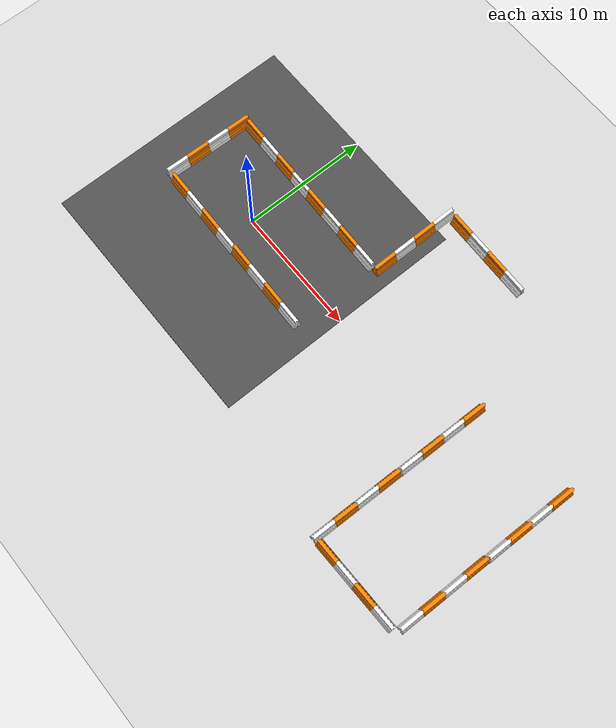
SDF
<sdf version="1.7">
 <world name="default">
  <light name="sun" type="directional">
   <pose>0 0 10 0 -0 0</pose>
   <diffuse>0.8 0.8 0.8 1</diffuse>
   <specular>0.2 0.2 0.2 1</specular>
   <attenuation>
    <range>1000</range>
    <constant>0.9</constant>
    <linear>0.01</linear>
    <quadratic>0.001</quadratic>
   </attenuation>
   <direction>-0.5 0.1 -0.9</direction>
   <spot><inner_angle>0</inner_angle><outer_angle>0</outer_angle><falloff>0</falloff></spot>
  </light>
  <model name="ground_plane">
   <static>1</static>
   <link name="link">
    <collision name="collision">
     <geometry><plane><normal>0 0 1</normal><size>100 100</size></plane></geometry>
     <surface><friction><ode><mu>100</mu><mu2>50</mu2></ode></friction></surface>
    </collision>
    <visual name="visual">
     <cast_shadows>0</cast_shadows>
     <geometry><plane><normal>0 0 1</normal><size>100 100</size></plane></geometry>
     <material>
      <script><uri>file://media/materials/scripts/gazebo.material</uri><name>Gazebo/Grey</name></script>
     </material>
    </visual>
   </link>
  </model>
  <model name="asphalt_plane">
   <static>1</static>
   <link name="link">
    <collision name="collision"><geometry><box><size>20 20 0.1</size></box></geometry></collision>
    <visual name="visual">
     <cast_shadows>0</cast_shadows>
     <geometry><box><size>20 20 0.1</size></box></geometry>
     <material>
      <script>
       <uri>model://asphalt_plane/materials/scripts</uri>
       <uri>model://asphalt_plane/materials/textures</uri>
       <name>vrc/asphalt</name>
      </script>
     </material>
    </visual>
   </link>
  </model>
  <physics name="default_physics" default="0" type="ode">
   <ode>
    <solver>
     <type>quick</type>
     <iters>10</iters>
     <sor>1.3</sor>
     <use_dynamic_moi_rescaling>0</use_dynamic_moi_rescaling>
    </solver>
    <constraints>
     <cfm>0</cfm>
     <erp>0.2</erp>
     <contact_max_correcting_vel>100</contact_max_correcting_vel>
     <contact_surface_layer>0.001</contact_surface_layer>
    </constraints>
   </ode>
   <max_step_size>0.004</max_step_size>
   <real_time_factor>1</real_time_factor>
   <real_time_update_rate>250</real_time_update_rate>
  </physics>
  <gravity>0 0 -9.8066</gravity>
  <magnetic_field>6e-06 2.3e-05 -4.2e-05</magnetic_field>
  <atmosphere type="adiabatic"/>
  <scene><ambient>0.4 0.4 0.4 1</ambient><background>0.7 0.7 0.7 1</background><shadows>1</shadows></scene>
  <model name="barrier">
   <link name="link">
    <pose>10.1496 5.51614 0 0 0 -0.785398</pose>
    <visual name="visual">
     <geometry>
      <mesh><uri>model://drc_practice_white_jersey_barrier/meshes/jersey_barrier.dae</uri></mesh>
     </geometry>
     <material><shader type="pixel"/></material>
    </visual>
    <collision name="collision">
     <geometry>
      <mesh>
       <uri>/home/ngc/.gazebo/models/drc_practice_white_jersey_barrier/meshes/jersey_barrier.dae</uri>
       <scale>1 1 1</scale>
      </mesh>
     </geometry>
     <surface>
      <friction>
       <ode><mu>1</mu><mu2>1</mu2><fdir1>0 0 0</fdir1><slip1>0</slip1><slip2>0</slip2></ode>
       <torsional>
        <coefficient>1</coefficient>
        <patch_radius>0</patch_radius>
        <surface_radius>0</surface_radius>
        <use_patch_radius>1</use_patch_radius>
        <ode><slip>0</slip></ode>
       </torsional>
      </friction>
      <bounce><restitution_coefficient>0</restitution_coefficient><threshold>1e+06</threshold></bounce>
      <contact>
       <collide_without_contact>0</collide_without_contact>
       <collide_without_contact_bitmask>1</collide_without_contact_bitmask>
       <collide_bitmask>1</collide_bitmask>
       <ode>
        <soft_cfm>0</soft_cfm>
        <soft_erp>0.2</soft_erp>
        <kp>1e+13</kp>
        <kd>1</kd>
        <max_vel>0.01</max_vel>
        <min_depth>0</min_depth>
       </ode>
       <bullet>
        <split_impulse>1</split_impulse>
        <split_impulse_penetration_threshold>-0.01</split_impulse_penetration_threshold>
        <soft_cfm>0</soft_cfm>
        <soft_erp>0.2</soft_erp>
        <kp>1e+13</kp>
        <kd>1</kd>
       </bullet>
      </contact>
     </surface>
    </collision>
   </link>
   <link name="five::link">
    <pose>6.3884 1.79074 0 0 0 -0.785398</pose>
    <visual name="visual">
     <geometry>
      <mesh><uri>model://drc_practice_orange_jersey_barrier/meshes/jersey_barrier.dae</uri></mesh>
     </geometry>
     <material><shader type="pixel"/></material>
    </visual>
    <collision name="collision">
     <geometry>
      <mesh>
       <uri>/home/ngc/.gazebo/models/drc_practice_orange_jersey_barrier/meshes/jersey_barrier.dae</uri>
       <scale>1 1 1</scale>
      </mesh>
     </geometry>
     <surface>
      <friction>
       <ode><mu>1</mu><mu2>1</mu2><fdir1>0 0 0</fdir1><slip1>0</slip1><slip2>0</slip2></ode>
       <torsional>
        <coefficient>1</coefficient>
        <patch_radius>0</patch_radius>
        <surface_radius>0</surface_radius>
        <use_patch_radius>1</use_patch_radius>
        <ode><slip>0</slip></ode>
       </torsional>
      </friction>
      <bounce><restitution_coefficient>0</restitution_coefficient><threshold>1e+06</threshold></bounce>
      <contact>
       <collide_without_contact>0</collide_without_contact>
       <collide_without_contact_bitmask>1</collide_without_contact_bitmask>
       <collide_bitmask>1</collide_bitmask>
       <ode>
        <soft_cfm>0</soft_cfm>
        <soft_erp>0.2</soft_erp>
        <kp>1e+13</kp>
        <kd>1</kd>
        <max_vel>0.01</max_vel>
        <min_depth>0</min_depth>
       </ode>
       <bullet>
        <split_impulse>1</split_impulse>
        <split_impulse_penetration_threshold>-0.01</split_impulse_penetration_threshold>
        <soft_cfm>0</soft_cfm>
        <soft_erp>0.2</soft_erp>
        <kp>1e+13</kp>
        <kd>1</kd>
       </bullet>
      </contact>
     </surface>
    </collision>
   </link>
   <link name="seven::link">
    <pose>8.89611 4.27529 0 0 0 -0.785398</pose>
    <visual name="visual">
     <geometry>
      <mesh><uri>model://drc_practice_orange_jersey_barrier/meshes/jersey_barrier.dae</uri></mesh>
     </geometry>
     <material><shader type="pixel"/></material>
    </visual>
    <collision name="collision">
     <geometry>
      <mesh>
       <uri>/home/ngc/.gazebo/models/drc_practice_orange_jersey_barrier/meshes/jersey_barrier.dae</uri>
       <scale>1 1 1</scale>
      </mesh>
     </geometry>
     <surface>
      <friction>
       <ode><mu>1</mu><mu2>1</mu2><fdir1>0 0 0</fdir1><slip1>0</slip1><slip2>0</slip2></ode>
       <torsional>
        <coefficient>1</coefficient>
        <patch_radius>0</patch_radius>
        <surface_radius>0</surface_radius>
        <use_patch_radius>1</use_patch_radius>
        <ode><slip>0</slip></ode>
       </torsional>
      </friction>
      <bounce><restitution_coefficient>0</restitution_coefficient><threshold>1e+06</threshold></bounce>
      <contact>
       <collide_without_contact>0</collide_without_contact>
       <collide_without_contact_bitmask>1</collide_without_contact_bitmask>
       <collide_bitmask>1</collide_bitmask>
       <ode>
        <soft_cfm>0</soft_cfm>
        <soft_erp>0.2</soft_erp>
        <kp>1e+13</kp>
        <kd>1</kd>
        <max_vel>0.01</max_vel>
        <min_depth>0</min_depth>
       </ode>
       <bullet>
        <split_impulse>1</split_impulse>
        <split_impulse_penetration_threshold>-0.01</split_impulse_penetration_threshold>
        <soft_cfm>0</soft_cfm>
        <soft_erp>0.2</soft_erp>
        <kp>1e+13</kp>
        <kd>1</kd>
       </bullet>
      </contact>
     </surface>
    </collision>
   </link>
   <link name="six::link">
    <pose>7.6423 3.03258 0 0 0 -0.785398</pose>
    <visual name="visual">
     <geometry>
      <mesh><uri>model://drc_practice_white_jersey_barrier/meshes/jersey_barrier.dae</uri></mesh>
     </geometry>
     <material><shader type="pixel"/></material>
    </visual>
    <collision name="collision">
     <geometry>
      <mesh>
       <uri>/home/ngc/.gazebo/models/drc_practice_white_jersey_barrier/meshes/jersey_barrier.dae</uri>
       <scale>1 1 1</scale>
      </mesh>
     </geometry>
     <surface>
      <friction>
       <ode><mu>1</mu><mu2>1</mu2><fdir1>0 0 0</fdir1><slip1>0</slip1><slip2>0</slip2></ode>
       <torsional>
        <coefficient>1</coefficient>
        <patch_radius>0</patch_radius>
        <surface_radius>0</surface_radius>
        <use_patch_radius>1</use_patch_radius>
        <ode><slip>0</slip></ode>
       </torsional>
      </friction>
      <bounce><restitution_coefficient>0</restitution_coefficient><threshold>1e+06</threshold></bounce>
      <contact>
       <collide_without_contact>0</collide_without_contact>
       <collide_without_contact_bitmask>1</collide_without_contact_bitmask>
       <collide_bitmask>1</collide_bitmask>
       <ode>
        <soft_cfm>0</soft_cfm>
        <soft_erp>0.2</soft_erp>
        <kp>1e+13</kp>
        <kd>1</kd>
        <max_vel>0.01</max_vel>
        <min_depth>0</min_depth>
       </ode>
       <bullet>
        <split_impulse>1</split_impulse>
        <split_impulse_penetration_threshold>-0.01</split_impulse_penetration_threshold>
        <soft_cfm>0</soft_cfm>
        <soft_erp>0.2</soft_erp>
        <kp>1e+13</kp>
        <kd>1</kd>
       </bullet>
      </contact>
     </surface>
    </collision>
   </link>
   <static>1</static>
   <pose>-2.67395 0.225919 3 0 0 -0.802882</pose>
  </model>
  <model name="barrier_clone">
   <link name="link">
    <pose>10.1496 5.51614 0 0 0 -0.785398</pose>
    <visual name="visual">
     <geometry>
      <mesh><uri>model://drc_practice_white_jersey_barrier/meshes/jersey_barrier.dae</uri></mesh>
     </geometry>
     <material><shader type="pixel"/></material>
    </visual>
    <collision name="collision">
     <geometry>
      <mesh>
       <uri>/home/ngc/.gazebo/models/drc_practice_white_jersey_barrier/meshes/jersey_barrier.dae</uri>
       <scale>1 1 1</scale>
      </mesh>
     </geometry>
     <surface>
      <friction>
       <ode><mu>1</mu><mu2>1</mu2><fdir1>0 0 0</fdir1><slip1>0</slip1><slip2>0</slip2></ode>
       <torsional>
        <coefficient>1</coefficient>
        <patch_radius>0</patch_radius>
        <surface_radius>0</surface_radius>
        <use_patch_radius>1</use_patch_radius>
        <ode><slip>0</slip></ode>
       </torsional>
      </friction>
      <bounce><restitution_coefficient>0</restitution_coefficient><threshold>1e+06</threshold></bounce>
      <contact>
       <collide_without_contact>0</collide_without_contact>
       <collide_without_contact_bitmask>1</collide_without_contact_bitmask>
       <collide_bitmask>1</collide_bitmask>
       <ode>
        <soft_cfm>0</soft_cfm>
        <soft_erp>0.2</soft_erp>
        <kp>1e+13</kp>
        <kd>1</kd>
        <max_vel>0.01</max_vel>
        <min_depth>0</min_depth>
       </ode>
       <bullet>
        <split_impulse>1</split_impulse>
        <split_impulse_penetration_threshold>-0.01</split_impulse_penetration_threshold>
        <soft_cfm>0</soft_cfm>
        <soft_erp>0.2</soft_erp>
        <kp>1e+13</kp>
        <kd>1</kd>
       </bullet>
      </contact>
     </surface>
    </collision>
   </link>
   <link name="five::link">
    <pose>6.3884 1.79074 0 0 0 -0.785398</pose>
    <visual name="visual">
     <geometry>
      <mesh><uri>model://drc_practice_orange_jersey_barrier/meshes/jersey_barrier.dae</uri></mesh>
     </geometry>
     <material><shader type="pixel"/></material>
    </visual>
    <collision name="collision">
     <geometry>
      <mesh>
       <uri>/home/ngc/.gazebo/models/drc_practice_orange_jersey_barrier/meshes/jersey_barrier.dae</uri>
       <scale>1 1 1</scale>
      </mesh>
     </geometry>
     <surface>
      <friction>
       <ode><mu>1</mu><mu2>1</mu2><fdir1>0 0 0</fdir1><slip1>0</slip1><slip2>0</slip2></ode>
       <torsional>
        <coefficient>1</coefficient>
        <patch_radius>0</patch_radius>
        <surface_radius>0</surface_radius>
        <use_patch_radius>1</use_patch_radius>
        <ode><slip>0</slip></ode>
       </torsional>
      </friction>
      <bounce><restitution_coefficient>0</restitution_coefficient><threshold>1e+06</threshold></bounce>
      <contact>
       <collide_without_contact>0</collide_without_contact>
       <collide_without_contact_bitmask>1</collide_without_contact_bitmask>
       <collide_bitmask>1</collide_bitmask>
       <ode>
        <soft_cfm>0</soft_cfm>
        <soft_erp>0.2</soft_erp>
        <kp>1e+13</kp>
        <kd>1</kd>
        <max_vel>0.01</max_vel>
        <min_depth>0</min_depth>
       </ode>
       <bullet>
        <split_impulse>1</split_impulse>
        <split_impulse_penetration_threshold>-0.01</split_impulse_penetration_threshold>
        <soft_cfm>0</soft_cfm>
        <soft_erp>0.2</soft_erp>
        <kp>1e+13</kp>
        <kd>1</kd>
       </bullet>
      </contact>
     </surface>
    </collision>
   </link>
   <link name="seven::link">
    <pose>8.89611 4.27529 0 0 0 -0.785398</pose>
    <visual name="visual">
     <geometry>
      <mesh><uri>model://drc_practice_orange_jersey_barrier/meshes/jersey_barrier.dae</uri></mesh>
     </geometry>
     <material><shader type="pixel"/></material>
    </visual>
    <collision name="collision">
     <geometry>
      <mesh>
       <uri>/home/ngc/.gazebo/models/drc_practice_orange_jersey_barrier/meshes/jersey_barrier.dae</uri>
       <scale>1 1 1</scale>
      </mesh>
     </geometry>
     <surface>
      <friction>
       <ode><mu>1</mu><mu2>1</mu2><fdir1>0 0 0</fdir1><slip1>0</slip1><slip2>0</slip2></ode>
       <torsional>
        <coefficient>1</coefficient>
        <patch_radius>0</patch_radius>
        <surface_radius>0</surface_radius>
        <use_patch_radius>1</use_patch_radius>
        <ode><slip>0</slip></ode>
       </torsional>
      </friction>
      <bounce><restitution_coefficient>0</restitution_coefficient><threshold>1e+06</threshold></bounce>
      <contact>
       <collide_without_contact>0</collide_without_contact>
       <collide_without_contact_bitmask>1</collide_without_contact_bitmask>
       <collide_bitmask>1</collide_bitmask>
       <ode>
        <soft_cfm>0</soft_cfm>
        <soft_erp>0.2</soft_erp>
        <kp>1e+13</kp>
        <kd>1</kd>
        <max_vel>0.01</max_vel>
        <min_depth>0</min_depth>
       </ode>
       <bullet>
        <split_impulse>1</split_impulse>
        <split_impulse_penetration_threshold>-0.01</split_impulse_penetration_threshold>
        <soft_cfm>0</soft_cfm>
        <soft_erp>0.2</soft_erp>
        <kp>1e+13</kp>
        <kd>1</kd>
       </bullet>
      </contact>
     </surface>
    </collision>
   </link>
   <link name="six::link">
    <pose>7.6423 3.03258 0 0 0 -0.785398</pose>
    <visual name="visual">
     <geometry>
      <mesh><uri>model://drc_practice_white_jersey_barrier/meshes/jersey_barrier.dae</uri></mesh>
     </geometry>
     <material><shader type="pixel"/></material>
    </visual>
    <collision name="collision">
     <geometry>
      <mesh>
       <uri>/home/ngc/.gazebo/models/drc_practice_white_jersey_barrier/meshes/jersey_barrier.dae</uri>
       <scale>1 1 1</scale>
      </mesh>
     </geometry>
     <surface>
      <friction>
       <ode><mu>1</mu><mu2>1</mu2><fdir1>0 0 0</fdir1><slip1>0</slip1><slip2>0</slip2></ode>
       <torsional>
        <coefficient>1</coefficient>
        <patch_radius>0</patch_radius>
        <surface_radius>0</surface_radius>
        <use_patch_radius>1</use_patch_radius>
        <ode><slip>0</slip></ode>
       </torsional>
      </friction>
      <bounce><restitution_coefficient>0</restitution_coefficient><threshold>1e+06</threshold></bounce>
      <contact>
       <collide_without_contact>0</collide_without_contact>
       <collide_without_contact_bitmask>1</collide_without_contact_bitmask>
       <collide_bitmask>1</collide_bitmask>
       <ode>
        <soft_cfm>0</soft_cfm>
        <soft_erp>0.2</soft_erp>
        <kp>1e+13</kp>
        <kd>1</kd>
        <max_vel>0.01</max_vel>
        <min_depth>0</min_depth>
       </ode>
       <bullet>
        <split_impulse>1</split_impulse>
        <split_impulse_penetration_threshold>-0.01</split_impulse_penetration_threshold>
        <soft_cfm>0</soft_cfm>
        <soft_erp>0.2</soft_erp>
        <kp>1e+13</kp>
        <kd>1</kd>
       </bullet>
      </contact>
     </surface>
    </collision>
   </link>
   <static>1</static>
   <pose>-2.67408 6.88591 3 0 0 -0.802882</pose>
  </model>
  <model name="barrier_clone_0">
   <link name="link">
    <pose>10.1496 5.51614 0 0 0 -0.785398</pose>
    <visual name="visual">
     <geometry>
      <mesh><uri>model://drc_practice_white_jersey_barrier/meshes/jersey_barrier.dae</uri></mesh>
     </geometry>
     <material><shader type="pixel"/></material>
    </visual>
    <collision name="collision">
     <geometry>
      <mesh>
       <uri>/home/ngc/.gazebo/models/drc_practice_white_jersey_barrier/meshes/jersey_barrier.dae</uri>
       <scale>1 1 1</scale>
      </mesh>
     </geometry>
     <surface>
      <friction>
       <ode><mu>1</mu><mu2>1</mu2><fdir1>0 0 0</fdir1><slip1>0</slip1><slip2>0</slip2></ode>
       <torsional>
        <coefficient>1</coefficient>
        <patch_radius>0</patch_radius>
        <surface_radius>0</surface_radius>
        <use_patch_radius>1</use_patch_radius>
        <ode><slip>0</slip></ode>
       </torsional>
      </friction>
      <bounce><restitution_coefficient>0</restitution_coefficient><threshold>1e+06</threshold></bounce>
      <contact>
       <collide_without_contact>0</collide_without_contact>
       <collide_without_contact_bitmask>1</collide_without_contact_bitmask>
       <collide_bitmask>1</collide_bitmask>
       <ode>
        <soft_cfm>0</soft_cfm>
        <soft_erp>0.2</soft_erp>
        <kp>1e+13</kp>
        <kd>1</kd>
        <max_vel>0.01</max_vel>
        <min_depth>0</min_depth>
       </ode>
       <bullet>
        <split_impulse>1</split_impulse>
        <split_impulse_penetration_threshold>-0.01</split_impulse_penetration_threshold>
        <soft_cfm>0</soft_cfm>
        <soft_erp>0.2</soft_erp>
        <kp>1e+13</kp>
        <kd>1</kd>
       </bullet>
      </contact>
     </surface>
    </collision>
   </link>
   <link name="five::link">
    <pose>6.3884 1.79074 0 0 0 -0.785398</pose>
    <visual name="visual">
     <geometry>
      <mesh><uri>model://drc_practice_orange_jersey_barrier/meshes/jersey_barrier.dae</uri></mesh>
     </geometry>
     <material><shader type="pixel"/></material>
    </visual>
    <collision name="collision">
     <geometry>
      <mesh>
       <uri>/home/ngc/.gazebo/models/drc_practice_orange_jersey_barrier/meshes/jersey_barrier.dae</uri>
       <scale>1 1 1</scale>
      </mesh>
     </geometry>
     <surface>
      <friction>
       <ode><mu>1</mu><mu2>1</mu2><fdir1>0 0 0</fdir1><slip1>0</slip1><slip2>0</slip2></ode>
       <torsional>
        <coefficient>1</coefficient>
        <patch_radius>0</patch_radius>
        <surface_radius>0</surface_radius>
        <use_patch_radius>1</use_patch_radius>
        <ode><slip>0</slip></ode>
       </torsional>
      </friction>
      <bounce><restitution_coefficient>0</restitution_coefficient><threshold>1e+06</threshold></bounce>
      <contact>
       <collide_without_contact>0</collide_without_contact>
       <collide_without_contact_bitmask>1</collide_without_contact_bitmask>
       <collide_bitmask>1</collide_bitmask>
       <ode>
        <soft_cfm>0</soft_cfm>
        <soft_erp>0.2</soft_erp>
        <kp>1e+13</kp>
        <kd>1</kd>
        <max_vel>0.01</max_vel>
        <min_depth>0</min_depth>
       </ode>
       <bullet>
        <split_impulse>1</split_impulse>
        <split_impulse_penetration_threshold>-0.01</split_impulse_penetration_threshold>
        <soft_cfm>0</soft_cfm>
        <soft_erp>0.2</soft_erp>
        <kp>1e+13</kp>
        <kd>1</kd>
       </bullet>
      </contact>
     </surface>
    </collision>
   </link>
   <link name="seven::link">
    <pose>8.89611 4.27529 0 0 0 -0.785398</pose>
    <visual name="visual">
     <geometry>
      <mesh><uri>model://drc_practice_orange_jersey_barrier/meshes/jersey_barrier.dae</uri></mesh>
     </geometry>
     <material><shader type="pixel"/></material>
    </visual>
    <collision name="collision">
     <geometry>
      <mesh>
       <uri>/home/ngc/.gazebo/models/drc_practice_orange_jersey_barrier/meshes/jersey_barrier.dae</uri>
       <scale>1 1 1</scale>
      </mesh>
     </geometry>
     <surface>
      <friction>
       <ode><mu>1</mu><mu2>1</mu2><fdir1>0 0 0</fdir1><slip1>0</slip1><slip2>0</slip2></ode>
       <torsional>
        <coefficient>1</coefficient>
        <patch_radius>0</patch_radius>
        <surface_radius>0</surface_radius>
        <use_patch_radius>1</use_patch_radius>
        <ode><slip>0</slip></ode>
       </torsional>
      </friction>
      <bounce><restitution_coefficient>0</restitution_coefficient><threshold>1e+06</threshold></bounce>
      <contact>
       <collide_without_contact>0</collide_without_contact>
       <collide_without_contact_bitmask>1</collide_without_contact_bitmask>
       <collide_bitmask>1</collide_bitmask>
       <ode>
        <soft_cfm>0</soft_cfm>
        <soft_erp>0.2</soft_erp>
        <kp>1e+13</kp>
        <kd>1</kd>
        <max_vel>0.01</max_vel>
        <min_depth>0</min_depth>
       </ode>
       <bullet>
        <split_impulse>1</split_impulse>
        <split_impulse_penetration_threshold>-0.01</split_impulse_penetration_threshold>
        <soft_cfm>0</soft_cfm>
        <soft_erp>0.2</soft_erp>
        <kp>1e+13</kp>
        <kd>1</kd>
       </bullet>
      </contact>
     </surface>
    </collision>
   </link>
   <link name="six::link">
    <pose>7.6423 3.03258 0 0 0 -0.785398</pose>
    <visual name="visual">
     <geometry>
      <mesh><uri>model://drc_practice_white_jersey_barrier/meshes/jersey_barrier.dae</uri></mesh>
     </geometry>
     <material><shader type="pixel"/></material>
    </visual>
    <collision name="collision">
     <geometry>
      <mesh>
       <uri>/home/ngc/.gazebo/models/drc_practice_white_jersey_barrier/meshes/jersey_barrier.dae</uri>
       <scale>1 1 1</scale>
      </mesh>
     </geometry>
     <surface>
      <friction>
       <ode><mu>1</mu><mu2>1</mu2><fdir1>0 0 0</fdir1><slip1>0</slip1><slip2>0</slip2></ode>
       <torsional>
        <coefficient>1</coefficient>
        <patch_radius>0</patch_radius>
        <surface_radius>0</surface_radius>
        <use_patch_radius>1</use_patch_radius>
        <ode><slip>0</slip></ode>
       </torsional>
      </friction>
      <bounce><restitution_coefficient>0</restitution_coefficient><threshold>1e+06</threshold></bounce>
      <contact>
       <collide_without_contact>0</collide_without_contact>
       <collide_without_contact_bitmask>1</collide_without_contact_bitmask>
       <collide_bitmask>1</collide_bitmask>
       <ode>
        <soft_cfm>0</soft_cfm>
        <soft_erp>0.2</soft_erp>
        <kp>1e+13</kp>
        <kd>1</kd>
        <max_vel>0.01</max_vel>
        <min_depth>0</min_depth>
       </ode>
       <bullet>
        <split_impulse>1</split_impulse>
        <split_impulse_penetration_threshold>-0.01</split_impulse_penetration_threshold>
        <soft_cfm>0</soft_cfm>
        <soft_erp>0.2</soft_erp>
        <kp>1e+13</kp>
        <kd>1</kd>
       </bullet>
      </contact>
     </surface>
    </collision>
   </link>
   <static>1</static>
   <pose>-1.84342 8.67192 3 0 0 -2.37547</pose>
  </model>
  <model name="barrier_clone_1">
   <link name="link">
    <pose>10.1496 5.51614 0 0 0 -0.785398</pose>
    <visual name="visual">
     <geometry>
      <mesh><uri>model://drc_practice_white_jersey_barrier/meshes/jersey_barrier.dae</uri></mesh>
     </geometry>
     <material><shader type="pixel"/></material>
    </visual>
    <collision name="collision">
     <geometry>
      <mesh>
       <uri>/home/ngc/.gazebo/models/drc_practice_white_jersey_barrier/meshes/jersey_barrier.dae</uri>
       <scale>1 1 1</scale>
      </mesh>
     </geometry>
     <surface>
      <friction>
       <ode><mu>1</mu><mu2>1</mu2><fdir1>0 0 0</fdir1><slip1>0</slip1><slip2>0</slip2></ode>
       <torsional>
        <coefficient>1</coefficient>
        <patch_radius>0</patch_radius>
        <surface_radius>0</surface_radius>
        <use_patch_radius>1</use_patch_radius>
        <ode><slip>0</slip></ode>
       </torsional>
      </friction>
      <bounce><restitution_coefficient>0</restitution_coefficient><threshold>1e+06</threshold></bounce>
      <contact>
       <collide_without_contact>0</collide_without_contact>
       <collide_without_contact_bitmask>1</collide_without_contact_bitmask>
       <collide_bitmask>1</collide_bitmask>
       <ode>
        <soft_cfm>0</soft_cfm>
        <soft_erp>0.2</soft_erp>
        <kp>1e+13</kp>
        <kd>1</kd>
        <max_vel>0.01</max_vel>
        <min_depth>0</min_depth>
       </ode>
       <bullet>
        <split_impulse>1</split_impulse>
        <split_impulse_penetration_threshold>-0.01</split_impulse_penetration_threshold>
        <soft_cfm>0</soft_cfm>
        <soft_erp>0.2</soft_erp>
        <kp>1e+13</kp>
        <kd>1</kd>
       </bullet>
      </contact>
     </surface>
    </collision>
   </link>
   <link name="five::link">
    <pose>6.3884 1.79074 0 0 0 -0.785398</pose>
    <visual name="visual">
     <geometry>
      <mesh><uri>model://drc_practice_orange_jersey_barrier/meshes/jersey_barrier.dae</uri></mesh>
     </geometry>
     <material><shader type="pixel"/></material>
    </visual>
    <collision name="collision">
     <geometry>
      <mesh>
       <uri>/home/ngc/.gazebo/models/drc_practice_orange_jersey_barrier/meshes/jersey_barrier.dae</uri>
       <scale>1 1 1</scale>
      </mesh>
     </geometry>
     <surface>
      <friction>
       <ode><mu>1</mu><mu2>1</mu2><fdir1>0 0 0</fdir1><slip1>0</slip1><slip2>0</slip2></ode>
       <torsional>
        <coefficient>1</coefficient>
        <patch_radius>0</patch_radius>
        <surface_radius>0</surface_radius>
        <use_patch_radius>1</use_patch_radius>
        <ode><slip>0</slip></ode>
       </torsional>
      </friction>
      <bounce><restitution_coefficient>0</restitution_coefficient><threshold>1e+06</threshold></bounce>
      <contact>
       <collide_without_contact>0</collide_without_contact>
       <collide_without_contact_bitmask>1</collide_without_contact_bitmask>
       <collide_bitmask>1</collide_bitmask>
       <ode>
        <soft_cfm>0</soft_cfm>
        <soft_erp>0.2</soft_erp>
        <kp>1e+13</kp>
        <kd>1</kd>
        <max_vel>0.01</max_vel>
        <min_depth>0</min_depth>
       </ode>
       <bullet>
        <split_impulse>1</split_impulse>
        <split_impulse_penetration_threshold>-0.01</split_impulse_penetration_threshold>
        <soft_cfm>0</soft_cfm>
        <soft_erp>0.2</soft_erp>
        <kp>1e+13</kp>
        <kd>1</kd>
       </bullet>
      </contact>
     </surface>
    </collision>
   </link>
   <link name="seven::link">
    <pose>8.89611 4.27529 0 0 0 -0.785398</pose>
    <visual name="visual">
     <geometry>
      <mesh><uri>model://drc_practice_orange_jersey_barrier/meshes/jersey_barrier.dae</uri></mesh>
     </geometry>
     <material><shader type="pixel"/></material>
    </visual>
    <collision name="collision">
     <geometry>
      <mesh>
       <uri>/home/ngc/.gazebo/models/drc_practice_orange_jersey_barrier/meshes/jersey_barrier.dae</uri>
       <scale>1 1 1</scale>
      </mesh>
     </geometry>
     <surface>
      <friction>
       <ode><mu>1</mu><mu2>1</mu2><fdir1>0 0 0</fdir1><slip1>0</slip1><slip2>0</slip2></ode>
       <torsional>
        <coefficient>1</coefficient>
        <patch_radius>0</patch_radius>
        <surface_radius>0</surface_radius>
        <use_patch_radius>1</use_patch_radius>
        <ode><slip>0</slip></ode>
       </torsional>
      </friction>
      <bounce><restitution_coefficient>0</restitution_coefficient><threshold>1e+06</threshold></bounce>
      <contact>
       <collide_without_contact>0</collide_without_contact>
       <collide_without_contact_bitmask>1</collide_without_contact_bitmask>
       <collide_bitmask>1</collide_bitmask>
       <ode>
        <soft_cfm>0</soft_cfm>
        <soft_erp>0.2</soft_erp>
        <kp>1e+13</kp>
        <kd>1</kd>
        <max_vel>0.01</max_vel>
        <min_depth>0</min_depth>
       </ode>
       <bullet>
        <split_impulse>1</split_impulse>
        <split_impulse_penetration_threshold>-0.01</split_impulse_penetration_threshold>
        <soft_cfm>0</soft_cfm>
        <soft_erp>0.2</soft_erp>
        <kp>1e+13</kp>
        <kd>1</kd>
       </bullet>
      </contact>
     </surface>
    </collision>
   </link>
   <link name="six::link">
    <pose>7.6423 3.03258 0 0 0 -0.785398</pose>
    <visual name="visual">
     <geometry>
      <mesh><uri>model://drc_practice_white_jersey_barrier/meshes/jersey_barrier.dae</uri></mesh>
     </geometry>
     <material><shader type="pixel"/></material>
    </visual>
    <collision name="collision">
     <geometry>
      <mesh>
       <uri>/home/ngc/.gazebo/models/drc_practice_white_jersey_barrier/meshes/jersey_barrier.dae</uri>
       <scale>1 1 1</scale>
      </mesh>
     </geometry>
     <surface>
      <friction>
       <ode><mu>1</mu><mu2>1</mu2><fdir1>0 0 0</fdir1><slip1>0</slip1><slip2>0</slip2></ode>
       <torsional>
        <coefficient>1</coefficient>
        <patch_radius>0</patch_radius>
        <surface_radius>0</surface_radius>
        <use_patch_radius>1</use_patch_radius>
        <ode><slip>0</slip></ode>
       </torsional>
      </friction>
      <bounce><restitution_coefficient>0</restitution_coefficient><threshold>1e+06</threshold></bounce>
      <contact>
       <collide_without_contact>0</collide_without_contact>
       <collide_without_contact_bitmask>1</collide_without_contact_bitmask>
       <collide_bitmask>1</collide_bitmask>
       <ode>
        <soft_cfm>0</soft_cfm>
        <soft_erp>0.2</soft_erp>
        <kp>1e+13</kp>
        <kd>1</kd>
        <max_vel>0.01</max_vel>
        <min_depth>0</min_depth>
       </ode>
       <bullet>
        <split_impulse>1</split_impulse>
        <split_impulse_penetration_threshold>-0.01</split_impulse_penetration_threshold>
        <soft_cfm>0</soft_cfm>
        <soft_erp>0.2</soft_erp>
        <kp>1e+13</kp>
        <kd>1</kd>
       </bullet>
      </contact>
     </surface>
    </collision>
   </link>
   <static>1</static>
   <pose>-9.71697 0.310372 3 0 0 -0.802882</pose>
  </model>
  <model name="barrier_clone_1_clone">
   <link name="link">
    <pose>10.1496 5.51614 0 0 0 -0.785398</pose>
    <visual name="visual">
     <geometry>
      <mesh><uri>model://drc_practice_white_jersey_barrier/meshes/jersey_barrier.dae</uri></mesh>
     </geometry>
     <material><shader type="pixel"/></material>
    </visual>
    <collision name="collision">
     <geometry>
      <mesh>
       <uri>/home/ngc/.gazebo/models/drc_practice_white_jersey_barrier/meshes/jersey_barrier.dae</uri>
       <scale>1 1 1</scale>
      </mesh>
     </geometry>
     <surface>
      <friction>
       <ode><mu>1</mu><mu2>1</mu2><fdir1>0 0 0</fdir1><slip1>0</slip1><slip2>0</slip2></ode>
       <torsional>
        <coefficient>1</coefficient>
        <patch_radius>0</patch_radius>
        <surface_radius>0</surface_radius>
        <use_patch_radius>1</use_patch_radius>
        <ode><slip>0</slip></ode>
       </torsional>
      </friction>
      <bounce><restitution_coefficient>0</restitution_coefficient><threshold>1e+06</threshold></bounce>
      <contact>
       <collide_without_contact>0</collide_without_contact>
       <collide_without_contact_bitmask>1</collide_without_contact_bitmask>
       <collide_bitmask>1</collide_bitmask>
       <ode>
        <soft_cfm>0</soft_cfm>
        <soft_erp>0.2</soft_erp>
        <kp>1e+13</kp>
        <kd>1</kd>
        <max_vel>0.01</max_vel>
        <min_depth>0</min_depth>
       </ode>
       <bullet>
        <split_impulse>1</split_impulse>
        <split_impulse_penetration_threshold>-0.01</split_impulse_penetration_threshold>
        <soft_cfm>0</soft_cfm>
        <soft_erp>0.2</soft_erp>
        <kp>1e+13</kp>
        <kd>1</kd>
       </bullet>
      </contact>
     </surface>
    </collision>
   </link>
   <link name="five::link">
    <pose>6.3884 1.79074 0 0 0 -0.785398</pose>
    <visual name="visual">
     <geometry>
      <mesh><uri>model://drc_practice_orange_jersey_barrier/meshes/jersey_barrier.dae</uri></mesh>
     </geometry>
     <material><shader type="pixel"/></material>
    </visual>
    <collision name="collision">
     <geometry>
      <mesh>
       <uri>/home/ngc/.gazebo/models/drc_practice_orange_jersey_barrier/meshes/jersey_barrier.dae</uri>
       <scale>1 1 1</scale>
      </mesh>
     </geometry>
     <surface>
      <friction>
       <ode><mu>1</mu><mu2>1</mu2><fdir1>0 0 0</fdir1><slip1>0</slip1><slip2>0</slip2></ode>
       <torsional>
        <coefficient>1</coefficient>
        <patch_radius>0</patch_radius>
        <surface_radius>0</surface_radius>
        <use_patch_radius>1</use_patch_radius>
        <ode><slip>0</slip></ode>
       </torsional>
      </friction>
      <bounce><restitution_coefficient>0</restitution_coefficient><threshold>1e+06</threshold></bounce>
      <contact>
       <collide_without_contact>0</collide_without_contact>
       <collide_without_contact_bitmask>1</collide_without_contact_bitmask>
       <collide_bitmask>1</collide_bitmask>
       <ode>
        <soft_cfm>0</soft_cfm>
        <soft_erp>0.2</soft_erp>
        <kp>1e+13</kp>
        <kd>1</kd>
        <max_vel>0.01</max_vel>
        <min_depth>0</min_depth>
       </ode>
       <bullet>
        <split_impulse>1</split_impulse>
        <split_impulse_penetration_threshold>-0.01</split_impulse_penetration_threshold>
        <soft_cfm>0</soft_cfm>
        <soft_erp>0.2</soft_erp>
        <kp>1e+13</kp>
        <kd>1</kd>
       </bullet>
      </contact>
     </surface>
    </collision>
   </link>
   <link name="seven::link">
    <pose>8.89611 4.27529 0 0 0 -0.785398</pose>
    <visual name="visual">
     <geometry>
      <mesh><uri>model://drc_practice_orange_jersey_barrier/meshes/jersey_barrier.dae</uri></mesh>
     </geometry>
     <material><shader type="pixel"/></material>
    </visual>
    <collision name="collision">
     <geometry>
      <mesh>
       <uri>/home/ngc/.gazebo/models/drc_practice_orange_jersey_barrier/meshes/jersey_barrier.dae</uri>
       <scale>1 1 1</scale>
      </mesh>
     </geometry>
     <surface>
      <friction>
       <ode><mu>1</mu><mu2>1</mu2><fdir1>0 0 0</fdir1><slip1>0</slip1><slip2>0</slip2></ode>
       <torsional>
        <coefficient>1</coefficient>
        <patch_radius>0</patch_radius>
        <surface_radius>0</surface_radius>
        <use_patch_radius>1</use_patch_radius>
        <ode><slip>0</slip></ode>
       </torsional>
      </friction>
      <bounce><restitution_coefficient>0</restitution_coefficient><threshold>1e+06</threshold></bounce>
      <contact>
       <collide_without_contact>0</collide_without_contact>
       <collide_without_contact_bitmask>1</collide_without_contact_bitmask>
       <collide_bitmask>1</collide_bitmask>
       <ode>
        <soft_cfm>0</soft_cfm>
        <soft_erp>0.2</soft_erp>
        <kp>1e+13</kp>
        <kd>1</kd>
        <max_vel>0.01</max_vel>
        <min_depth>0</min_depth>
       </ode>
       <bullet>
        <split_impulse>1</split_impulse>
        <split_impulse_penetration_threshold>-0.01</split_impulse_penetration_threshold>
        <soft_cfm>0</soft_cfm>
        <soft_erp>0.2</soft_erp>
        <kp>1e+13</kp>
        <kd>1</kd>
       </bullet>
      </contact>
     </surface>
    </collision>
   </link>
   <link name="six::link">
    <pose>7.6423 3.03258 0 0 0 -0.785398</pose>
    <visual name="visual">
     <geometry>
      <mesh><uri>model://drc_practice_white_jersey_barrier/meshes/jersey_barrier.dae</uri></mesh>
     </geometry>
     <material><shader type="pixel"/></material>
    </visual>
    <collision name="collision">
     <geometry>
      <mesh>
       <uri>/home/ngc/.gazebo/models/drc_practice_white_jersey_barrier/meshes/jersey_barrier.dae</uri>
       <scale>1 1 1</scale>
      </mesh>
     </geometry>
     <surface>
      <friction>
       <ode><mu>1</mu><mu2>1</mu2><fdir1>0 0 0</fdir1><slip1>0</slip1><slip2>0</slip2></ode>
       <torsional>
        <coefficient>1</coefficient>
        <patch_radius>0</patch_radius>
        <surface_radius>0</surface_radius>
        <use_patch_radius>1</use_patch_radius>
        <ode><slip>0</slip></ode>
       </torsional>
      </friction>
      <bounce><restitution_coefficient>0</restitution_coefficient><threshold>1e+06</threshold></bounce>
      <contact>
       <collide_without_contact>0</collide_without_contact>
       <collide_without_contact_bitmask>1</collide_without_contact_bitmask>
       <collide_bitmask>1</collide_bitmask>
       <ode>
        <soft_cfm>0</soft_cfm>
        <soft_erp>0.2</soft_erp>
        <kp>1e+13</kp>
        <kd>1</kd>
        <max_vel>0.01</max_vel>
        <min_depth>0</min_depth>
       </ode>
       <bullet>
        <split_impulse>1</split_impulse>
        <split_impulse_penetration_threshold>-0.01</split_impulse_penetration_threshold>
        <soft_cfm>0</soft_cfm>
        <soft_erp>0.2</soft_erp>
        <kp>1e+13</kp>
        <kd>1</kd>
       </bullet>
      </contact>
     </surface>
    </collision>
   </link>
   <static>1</static>
   <pose>-9.73137 7.02171 3 0 0 -0.802882</pose>
  </model>
  <model name="barrier_clone_clone">
   <link name="link">
    <pose>10.1496 5.51614 0 0 0 -0.785398</pose>
    <visual name="visual">
     <geometry>
      <mesh><uri>model://drc_practice_white_jersey_barrier/meshes/jersey_barrier.dae</uri></mesh>
     </geometry>
     <material><shader type="pixel"/></material>
    </visual>
    <collision name="collision">
     <geometry>
      <mesh>
       <uri>/home/ngc/.gazebo/models/drc_practice_white_jersey_barrier/meshes/jersey_barrier.dae</uri>
       <scale>1 1 1</scale>
      </mesh>
     </geometry>
     <surface>
      <friction>
       <ode><mu>1</mu><mu2>1</mu2><fdir1>0 0 0</fdir1><slip1>0</slip1><slip2>0</slip2></ode>
       <torsional>
        <coefficient>1</coefficient>
        <patch_radius>0</patch_radius>
        <surface_radius>0</surface_radius>
        <use_patch_radius>1</use_patch_radius>
        <ode><slip>0</slip></ode>
       </torsional>
      </friction>
      <bounce><restitution_coefficient>0</restitution_coefficient><threshold>1e+06</threshold></bounce>
      <contact>
       <collide_without_contact>0</collide_without_contact>
       <collide_without_contact_bitmask>1</collide_without_contact_bitmask>
       <collide_bitmask>1</collide_bitmask>
       <ode>
        <soft_cfm>0</soft_cfm>
        <soft_erp>0.2</soft_erp>
        <kp>1e+13</kp>
        <kd>1</kd>
        <max_vel>0.01</max_vel>
        <min_depth>0</min_depth>
       </ode>
       <bullet>
        <split_impulse>1</split_impulse>
        <split_impulse_penetration_threshold>-0.01</split_impulse_penetration_threshold>
        <soft_cfm>0</soft_cfm>
        <soft_erp>0.2</soft_erp>
        <kp>1e+13</kp>
        <kd>1</kd>
       </bullet>
      </contact>
     </surface>
    </collision>
   </link>
   <link name="five::link">
    <pose>6.3884 1.79074 0 0 0 -0.785398</pose>
    <visual name="visual">
     <geometry>
      <mesh><uri>model://drc_practice_orange_jersey_barrier/meshes/jersey_barrier.dae</uri></mesh>
     </geometry>
     <material><shader type="pixel"/></material>
    </visual>
    <collision name="collision">
     <geometry>
      <mesh>
       <uri>/home/ngc/.gazebo/models/drc_practice_orange_jersey_barrier/meshes/jersey_barrier.dae</uri>
       <scale>1 1 1</scale>
      </mesh>
     </geometry>
     <surface>
      <friction>
       <ode><mu>1</mu><mu2>1</mu2><fdir1>0 0 0</fdir1><slip1>0</slip1><slip2>0</slip2></ode>
       <torsional>
        <coefficient>1</coefficient>
        <patch_radius>0</patch_radius>
        <surface_radius>0</surface_radius>
        <use_patch_radius>1</use_patch_radius>
        <ode><slip>0</slip></ode>
       </torsional>
      </friction>
      <bounce><restitution_coefficient>0</restitution_coefficient><threshold>1e+06</threshold></bounce>
      <contact>
       <collide_without_contact>0</collide_without_contact>
       <collide_without_contact_bitmask>1</collide_without_contact_bitmask>
       <collide_bitmask>1</collide_bitmask>
       <ode>
        <soft_cfm>0</soft_cfm>
        <soft_erp>0.2</soft_erp>
        <kp>1e+13</kp>
        <kd>1</kd>
        <max_vel>0.01</max_vel>
        <min_depth>0</min_depth>
       </ode>
       <bullet>
        <split_impulse>1</split_impulse>
        <split_impulse_penetration_threshold>-0.01</split_impulse_penetration_threshold>
        <soft_cfm>0</soft_cfm>
        <soft_erp>0.2</soft_erp>
        <kp>1e+13</kp>
        <kd>1</kd>
       </bullet>
      </contact>
     </surface>
    </collision>
   </link>
   <link name="seven::link">
    <pose>8.89611 4.27529 0 0 0 -0.785398</pose>
    <visual name="visual">
     <geometry>
      <mesh><uri>model://drc_practice_orange_jersey_barrier/meshes/jersey_barrier.dae</uri></mesh>
     </geometry>
     <material><shader type="pixel"/></material>
    </visual>
    <collision name="collision">
     <geometry>
      <mesh>
       <uri>/home/ngc/.gazebo/models/drc_practice_orange_jersey_barrier/meshes/jersey_barrier.dae</uri>
       <scale>1 1 1</scale>
      </mesh>
     </geometry>
     <surface>
      <friction>
       <ode><mu>1</mu><mu2>1</mu2><fdir1>0 0 0</fdir1><slip1>0</slip1><slip2>0</slip2></ode>
       <torsional>
        <coefficient>1</coefficient>
        <patch_radius>0</patch_radius>
        <surface_radius>0</surface_radius>
        <use_patch_radius>1</use_patch_radius>
        <ode><slip>0</slip></ode>
       </torsional>
      </friction>
      <bounce><restitution_coefficient>0</restitution_coefficient><threshold>1e+06</threshold></bounce>
      <contact>
       <collide_without_contact>0</collide_without_contact>
       <collide_without_contact_bitmask>1</collide_without_contact_bitmask>
       <collide_bitmask>1</collide_bitmask>
       <ode>
        <soft_cfm>0</soft_cfm>
        <soft_erp>0.2</soft_erp>
        <kp>1e+13</kp>
        <kd>1</kd>
        <max_vel>0.01</max_vel>
        <min_depth>0</min_depth>
       </ode>
       <bullet>
        <split_impulse>1</split_impulse>
        <split_impulse_penetration_threshold>-0.01</split_impulse_penetration_threshold>
        <soft_cfm>0</soft_cfm>
        <soft_erp>0.2</soft_erp>
        <kp>1e+13</kp>
        <kd>1</kd>
       </bullet>
      </contact>
     </surface>
    </collision>
   </link>
   <link name="six::link">
    <pose>7.6423 3.03258 0 0 0 -0.785398</pose>
    <visual name="visual">
     <geometry>
      <mesh><uri>model://drc_practice_white_jersey_barrier/meshes/jersey_barrier.dae</uri></mesh>
     </geometry>
     <material><shader type="pixel"/></material>
    </visual>
    <collision name="collision">
     <geometry>
      <mesh>
       <uri>/home/ngc/.gazebo/models/drc_practice_white_jersey_barrier/meshes/jersey_barrier.dae</uri>
       <scale>1 1 1</scale>
      </mesh>
     </geometry>
     <surface>
      <friction>
       <ode><mu>1</mu><mu2>1</mu2><fdir1>0 0 0</fdir1><slip1>0</slip1><slip2>0</slip2></ode>
       <torsional>
        <coefficient>1</coefficient>
        <patch_radius>0</patch_radius>
        <surface_radius>0</surface_radius>
        <use_patch_radius>1</use_patch_radius>
        <ode><slip>0</slip></ode>
       </torsional>
      </friction>
      <bounce><restitution_coefficient>0</restitution_coefficient><threshold>1e+06</threshold></bounce>
      <contact>
       <collide_without_contact>0</collide_without_contact>
       <collide_without_contact_bitmask>1</collide_without_contact_bitmask>
       <collide_bitmask>1</collide_bitmask>
       <ode>
        <soft_cfm>0</soft_cfm>
        <soft_erp>0.2</soft_erp>
        <kp>1e+13</kp>
        <kd>1</kd>
        <max_vel>0.01</max_vel>
        <min_depth>0</min_depth>
       </ode>
       <bullet>
        <split_impulse>1</split_impulse>
        <split_impulse_penetration_threshold>-0.01</split_impulse_penetration_threshold>
        <soft_cfm>0</soft_cfm>
        <soft_erp>0.2</soft_erp>
        <kp>1e+13</kp>
        <kd>1</kd>
       </bullet>
      </contact>
     </surface>
    </collision>
   </link>
   <static>1</static>
   <pose>6.3342 -1.56565 3 0 -0 0.78886</pose>
  </model>
  <model name="barrier_clone_clone_0">
   <link name="link">
    <pose>10.1496 5.51614 0 0 0 -0.785398</pose>
    <visual name="visual">
     <geometry>
      <mesh><uri>model://drc_practice_white_jersey_barrier/meshes/jersey_barrier.dae</uri></mesh>
     </geometry>
     <material><shader type="pixel"/></material>
    </visual>
    <collision name="collision">
     <geometry>
      <mesh>
       <uri>/home/ngc/.gazebo/models/drc_practice_white_jersey_barrier/meshes/jersey_barrier.dae</uri>
       <scale>1 1 1</scale>
      </mesh>
     </geometry>
     <surface>
      <friction>
       <ode><mu>1</mu><mu2>1</mu2><fdir1>0 0 0</fdir1><slip1>0</slip1><slip2>0</slip2></ode>
       <torsional>
        <coefficient>1</coefficient>
        <patch_radius>0</patch_radius>
        <surface_radius>0</surface_radius>
        <use_patch_radius>1</use_patch_radius>
        <ode><slip>0</slip></ode>
       </torsional>
      </friction>
      <bounce><restitution_coefficient>0</restitution_coefficient><threshold>1e+06</threshold></bounce>
      <contact>
       <collide_without_contact>0</collide_without_contact>
       <collide_without_contact_bitmask>1</collide_without_contact_bitmask>
       <collide_bitmask>1</collide_bitmask>
       <ode>
        <soft_cfm>0</soft_cfm>
        <soft_erp>0.2</soft_erp>
        <kp>1e+13</kp>
        <kd>1</kd>
        <max_vel>0.01</max_vel>
        <min_depth>0</min_depth>
       </ode>
       <bullet>
        <split_impulse>1</split_impulse>
        <split_impulse_penetration_threshold>-0.01</split_impulse_penetration_threshold>
        <soft_cfm>0</soft_cfm>
        <soft_erp>0.2</soft_erp>
        <kp>1e+13</kp>
        <kd>1</kd>
       </bullet>
      </contact>
     </surface>
    </collision>
   </link>
   <link name="five::link">
    <pose>6.3884 1.79074 0 0 0 -0.785398</pose>
    <visual name="visual">
     <geometry>
      <mesh><uri>model://drc_practice_orange_jersey_barrier/meshes/jersey_barrier.dae</uri></mesh>
     </geometry>
     <material><shader type="pixel"/></material>
    </visual>
    <collision name="collision">
     <geometry>
      <mesh>
       <uri>/home/ngc/.gazebo/models/drc_practice_orange_jersey_barrier/meshes/jersey_barrier.dae</uri>
       <scale>1 1 1</scale>
      </mesh>
     </geometry>
     <surface>
      <friction>
       <ode><mu>1</mu><mu2>1</mu2><fdir1>0 0 0</fdir1><slip1>0</slip1><slip2>0</slip2></ode>
       <torsional>
        <coefficient>1</coefficient>
        <patch_radius>0</patch_radius>
        <surface_radius>0</surface_radius>
        <use_patch_radius>1</use_patch_radius>
        <ode><slip>0</slip></ode>
       </torsional>
      </friction>
      <bounce><restitution_coefficient>0</restitution_coefficient><threshold>1e+06</threshold></bounce>
      <contact>
       <collide_without_contact>0</collide_without_contact>
       <collide_without_contact_bitmask>1</collide_without_contact_bitmask>
       <collide_bitmask>1</collide_bitmask>
       <ode>
        <soft_cfm>0</soft_cfm>
        <soft_erp>0.2</soft_erp>
        <kp>1e+13</kp>
        <kd>1</kd>
        <max_vel>0.01</max_vel>
        <min_depth>0</min_depth>
       </ode>
       <bullet>
        <split_impulse>1</split_impulse>
        <split_impulse_penetration_threshold>-0.01</split_impulse_penetration_threshold>
        <soft_cfm>0</soft_cfm>
        <soft_erp>0.2</soft_erp>
        <kp>1e+13</kp>
        <kd>1</kd>
       </bullet>
      </contact>
     </surface>
    </collision>
   </link>
   <link name="seven::link">
    <pose>8.89611 4.27529 0 0 0 -0.785398</pose>
    <visual name="visual">
     <geometry>
      <mesh><uri>model://drc_practice_orange_jersey_barrier/meshes/jersey_barrier.dae</uri></mesh>
     </geometry>
     <material><shader type="pixel"/></material>
    </visual>
    <collision name="collision">
     <geometry>
      <mesh>
       <uri>/home/ngc/.gazebo/models/drc_practice_orange_jersey_barrier/meshes/jersey_barrier.dae</uri>
       <scale>1 1 1</scale>
      </mesh>
     </geometry>
     <surface>
      <friction>
       <ode><mu>1</mu><mu2>1</mu2><fdir1>0 0 0</fdir1><slip1>0</slip1><slip2>0</slip2></ode>
       <torsional>
        <coefficient>1</coefficient>
        <patch_radius>0</patch_radius>
        <surface_radius>0</surface_radius>
        <use_patch_radius>1</use_patch_radius>
        <ode><slip>0</slip></ode>
       </torsional>
      </friction>
      <bounce><restitution_coefficient>0</restitution_coefficient><threshold>1e+06</threshold></bounce>
      <contact>
       <collide_without_contact>0</collide_without_contact>
       <collide_without_contact_bitmask>1</collide_without_contact_bitmask>
       <collide_bitmask>1</collide_bitmask>
       <ode>
        <soft_cfm>0</soft_cfm>
        <soft_erp>0.2</soft_erp>
        <kp>1e+13</kp>
        <kd>1</kd>
        <max_vel>0.01</max_vel>
        <min_depth>0</min_depth>
       </ode>
       <bullet>
        <split_impulse>1</split_impulse>
        <split_impulse_penetration_threshold>-0.01</split_impulse_penetration_threshold>
        <soft_cfm>0</soft_cfm>
        <soft_erp>0.2</soft_erp>
        <kp>1e+13</kp>
        <kd>1</kd>
       </bullet>
      </contact>
     </surface>
    </collision>
   </link>
   <link name="six::link">
    <pose>7.6423 3.03258 0 0 0 -0.785398</pose>
    <visual name="visual">
     <geometry>
      <mesh><uri>model://drc_practice_white_jersey_barrier/meshes/jersey_barrier.dae</uri></mesh>
     </geometry>
     <material><shader type="pixel"/></material>
    </visual>
    <collision name="collision">
     <geometry>
      <mesh>
       <uri>/home/ngc/.gazebo/models/drc_practice_white_jersey_barrier/meshes/jersey_barrier.dae</uri>
       <scale>1 1 1</scale>
      </mesh>
     </geometry>
     <surface>
      <friction>
       <ode><mu>1</mu><mu2>1</mu2><fdir1>0 0 0</fdir1><slip1>0</slip1><slip2>0</slip2></ode>
       <torsional>
        <coefficient>1</coefficient>
        <patch_radius>0</patch_radius>
        <surface_radius>0</surface_radius>
        <use_patch_radius>1</use_patch_radius>
        <ode><slip>0</slip></ode>
       </torsional>
      </friction>
      <bounce><restitution_coefficient>0</restitution_coefficient><threshold>1e+06</threshold></bounce>
      <contact>
       <collide_without_contact>0</collide_without_contact>
       <collide_without_contact_bitmask>1</collide_without_contact_bitmask>
       <collide_bitmask>1</collide_bitmask>
       <ode>
        <soft_cfm>0</soft_cfm>
        <soft_erp>0.2</soft_erp>
        <kp>1e+13</kp>
        <kd>1</kd>
        <max_vel>0.01</max_vel>
        <min_depth>0</min_depth>
       </ode>
       <bullet>
        <split_impulse>1</split_impulse>
        <split_impulse_penetration_threshold>-0.01</split_impulse_penetration_threshold>
        <soft_cfm>0</soft_cfm>
        <soft_erp>0.2</soft_erp>
        <kp>1e+13</kp>
        <kd>1</kd>
       </bullet>
      </contact>
     </surface>
    </collision>
   </link>
   <static>1</static>
   <pose>5.19237 13.5218 3 0 0 -0.802882</pose>
  </model>
  <model name="barrier_clone_0_clone">
   <link name="link">
    <pose>10.1496 5.51614 0 0 0 -0.785398</pose>
    <visual name="visual">
     <geometry>
      <mesh><uri>model://drc_practice_white_jersey_barrier/meshes/jersey_barrier.dae</uri></mesh>
     </geometry>
     <material><shader type="pixel"/></material>
    </visual>
    <collision name="collision">
     <geometry>
      <mesh>
       <uri>/home/ngc/.gazebo/models/drc_practice_white_jersey_barrier/meshes/jersey_barrier.dae</uri>
       <scale>1 1 1</scale>
      </mesh>
     </geometry>
     <surface>
      <friction>
       <ode><mu>1</mu><mu2>1</mu2><fdir1>0 0 0</fdir1><slip1>0</slip1><slip2>0</slip2></ode>
       <torsional>
        <coefficient>1</coefficient>
        <patch_radius>0</patch_radius>
        <surface_radius>0</surface_radius>
        <use_patch_radius>1</use_patch_radius>
        <ode><slip>0</slip></ode>
       </torsional>
      </friction>
      <bounce><restitution_coefficient>0</restitution_coefficient><threshold>1e+06</threshold></bounce>
      <contact>
       <collide_without_contact>0</collide_without_contact>
       <collide_without_contact_bitmask>1</collide_without_contact_bitmask>
       <collide_bitmask>1</collide_bitmask>
       <ode>
        <soft_cfm>0</soft_cfm>
        <soft_erp>0.2</soft_erp>
        <kp>1e+13</kp>
        <kd>1</kd>
        <max_vel>0.01</max_vel>
        <min_depth>0</min_depth>
       </ode>
       <bullet>
        <split_impulse>1</split_impulse>
        <split_impulse_penetration_threshold>-0.01</split_impulse_penetration_threshold>
        <soft_cfm>0</soft_cfm>
        <soft_erp>0.2</soft_erp>
        <kp>1e+13</kp>
        <kd>1</kd>
       </bullet>
      </contact>
     </surface>
    </collision>
   </link>
   <link name="five::link">
    <pose>6.3884 1.79074 0 0 0 -0.785398</pose>
    <visual name="visual">
     <geometry>
      <mesh><uri>model://drc_practice_orange_jersey_barrier/meshes/jersey_barrier.dae</uri></mesh>
     </geometry>
     <material><shader type="pixel"/></material>
    </visual>
    <collision name="collision">
     <geometry>
      <mesh>
       <uri>/home/ngc/.gazebo/models/drc_practice_orange_jersey_barrier/meshes/jersey_barrier.dae</uri>
       <scale>1 1 1</scale>
      </mesh>
     </geometry>
     <surface>
      <friction>
       <ode><mu>1</mu><mu2>1</mu2><fdir1>0 0 0</fdir1><slip1>0</slip1><slip2>0</slip2></ode>
       <torsional>
        <coefficient>1</coefficient>
        <patch_radius>0</patch_radius>
        <surface_radius>0</surface_radius>
        <use_patch_radius>1</use_patch_radius>
        <ode><slip>0</slip></ode>
       </torsional>
      </friction>
      <bounce><restitution_coefficient>0</restitution_coefficient><threshold>1e+06</threshold></bounce>
      <contact>
       <collide_without_contact>0</collide_without_contact>
       <collide_without_contact_bitmask>1</collide_without_contact_bitmask>
       <collide_bitmask>1</collide_bitmask>
       <ode>
        <soft_cfm>0</soft_cfm>
        <soft_erp>0.2</soft_erp>
        <kp>1e+13</kp>
        <kd>1</kd>
        <max_vel>0.01</max_vel>
        <min_depth>0</min_depth>
       </ode>
       <bullet>
        <split_impulse>1</split_impulse>
        <split_impulse_penetration_threshold>-0.01</split_impulse_penetration_threshold>
        <soft_cfm>0</soft_cfm>
        <soft_erp>0.2</soft_erp>
        <kp>1e+13</kp>
        <kd>1</kd>
       </bullet>
      </contact>
     </surface>
    </collision>
   </link>
   <link name="seven::link">
    <pose>8.89611 4.27529 0 0 0 -0.785398</pose>
    <visual name="visual">
     <geometry>
      <mesh><uri>model://drc_practice_orange_jersey_barrier/meshes/jersey_barrier.dae</uri></mesh>
     </geometry>
     <material><shader type="pixel"/></material>
    </visual>
    <collision name="collision">
     <geometry>
      <mesh>
       <uri>/home/ngc/.gazebo/models/drc_practice_orange_jersey_barrier/meshes/jersey_barrier.dae</uri>
       <scale>1 1 1</scale>
      </mesh>
     </geometry>
     <surface>
      <friction>
       <ode><mu>1</mu><mu2>1</mu2><fdir1>0 0 0</fdir1><slip1>0</slip1><slip2>0</slip2></ode>
       <torsional>
        <coefficient>1</coefficient>
        <patch_radius>0</patch_radius>
        <surface_radius>0</surface_radius>
        <use_patch_radius>1</use_patch_radius>
        <ode><slip>0</slip></ode>
       </torsional>
      </friction>
      <bounce><restitution_coefficient>0</restitution_coefficient><threshold>1e+06</threshold></bounce>
      <contact>
       <collide_without_contact>0</collide_without_contact>
       <collide_without_contact_bitmask>1</collide_without_contact_bitmask>
       <collide_bitmask>1</collide_bitmask>
       <ode>
        <soft_cfm>0</soft_cfm>
        <soft_erp>0.2</soft_erp>
        <kp>1e+13</kp>
        <kd>1</kd>
        <max_vel>0.01</max_vel>
        <min_depth>0</min_depth>
       </ode>
       <bullet>
        <split_impulse>1</split_impulse>
        <split_impulse_penetration_threshold>-0.01</split_impulse_penetration_threshold>
        <soft_cfm>0</soft_cfm>
        <soft_erp>0.2</soft_erp>
        <kp>1e+13</kp>
        <kd>1</kd>
       </bullet>
      </contact>
     </surface>
    </collision>
   </link>
   <link name="six::link">
    <pose>7.6423 3.03258 0 0 0 -0.785398</pose>
    <visual name="visual">
     <geometry>
      <mesh><uri>model://drc_practice_white_jersey_barrier/meshes/jersey_barrier.dae</uri></mesh>
     </geometry>
     <material><shader type="pixel"/></material>
    </visual>
    <collision name="collision">
     <geometry>
      <mesh>
       <uri>/home/ngc/.gazebo/models/drc_practice_white_jersey_barrier/meshes/jersey_barrier.dae</uri>
       <scale>1 1 1</scale>
      </mesh>
     </geometry>
     <surface>
      <friction>
       <ode><mu>1</mu><mu2>1</mu2><fdir1>0 0 0</fdir1><slip1>0</slip1><slip2>0</slip2></ode>
       <torsional>
        <coefficient>1</coefficient>
        <patch_radius>0</patch_radius>
        <surface_radius>0</surface_radius>
        <use_patch_radius>1</use_patch_radius>
        <ode><slip>0</slip></ode>
       </torsional>
      </friction>
      <bounce><restitution_coefficient>0</restitution_coefficient><threshold>1e+06</threshold></bounce>
      <contact>
       <collide_without_contact>0</collide_without_contact>
       <collide_without_contact_bitmask>1</collide_without_contact_bitmask>
       <collide_bitmask>1</collide_bitmask>
       <ode>
        <soft_cfm>0</soft_cfm>
        <soft_erp>0.2</soft_erp>
        <kp>1e+13</kp>
        <kd>1</kd>
        <max_vel>0.01</max_vel>
        <min_depth>0</min_depth>
       </ode>
       <bullet>
        <split_impulse>1</split_impulse>
        <split_impulse_penetration_threshold>-0.01</split_impulse_penetration_threshold>
        <soft_cfm>0</soft_cfm>
        <soft_erp>0.2</soft_erp>
        <kp>1e+13</kp>
        <kd>1</kd>
       </bullet>
      </contact>
     </surface>
    </collision>
   </link>
   <static>1</static>
   <pose>32.3527 8.10174 3 0 0 -2.37547</pose>
  </model>
  <model name="barrier_clone_0_clone_clone">
   <link name="link">
    <pose>10.1496 5.51614 0 0 0 -0.785398</pose>
    <visual name="visual">
     <geometry>
      <mesh><uri>model://drc_practice_white_jersey_barrier/meshes/jersey_barrier.dae</uri></mesh>
     </geometry>
     <material><shader type="pixel"/></material>
    </visual>
    <collision name="collision">
     <geometry>
      <mesh>
       <uri>/home/ngc/.gazebo/models/drc_practice_white_jersey_barrier/meshes/jersey_barrier.dae</uri>
       <scale>1 1 1</scale>
      </mesh>
     </geometry>
     <surface>
      <friction>
       <ode><mu>1</mu><mu2>1</mu2><fdir1>0 0 0</fdir1><slip1>0</slip1><slip2>0</slip2></ode>
       <torsional>
        <coefficient>1</coefficient>
        <patch_radius>0</patch_radius>
        <surface_radius>0</surface_radius>
        <use_patch_radius>1</use_patch_radius>
        <ode><slip>0</slip></ode>
       </torsional>
      </friction>
      <bounce><restitution_coefficient>0</restitution_coefficient><threshold>1e+06</threshold></bounce>
      <contact>
       <collide_without_contact>0</collide_without_contact>
       <collide_without_contact_bitmask>1</collide_without_contact_bitmask>
       <collide_bitmask>1</collide_bitmask>
       <ode>
        <soft_cfm>0</soft_cfm>
        <soft_erp>0.2</soft_erp>
        <kp>1e+13</kp>
        <kd>1</kd>
        <max_vel>0.01</max_vel>
        <min_depth>0</min_depth>
       </ode>
       <bullet>
        <split_impulse>1</split_impulse>
        <split_impulse_penetration_threshold>-0.01</split_impulse_penetration_threshold>
        <soft_cfm>0</soft_cfm>
        <soft_erp>0.2</soft_erp>
        <kp>1e+13</kp>
        <kd>1</kd>
       </bullet>
      </contact>
     </surface>
    </collision>
   </link>
   <link name="five::link">
    <pose>6.3884 1.79074 0 0 0 -0.785398</pose>
    <visual name="visual">
     <geometry>
      <mesh><uri>model://drc_practice_orange_jersey_barrier/meshes/jersey_barrier.dae</uri></mesh>
     </geometry>
     <material><shader type="pixel"/></material>
    </visual>
    <collision name="collision">
     <geometry>
      <mesh>
       <uri>/home/ngc/.gazebo/models/drc_practice_orange_jersey_barrier/meshes/jersey_barrier.dae</uri>
       <scale>1 1 1</scale>
      </mesh>
     </geometry>
     <surface>
      <friction>
       <ode><mu>1</mu><mu2>1</mu2><fdir1>0 0 0</fdir1><slip1>0</slip1><slip2>0</slip2></ode>
       <torsional>
        <coefficient>1</coefficient>
        <patch_radius>0</patch_radius>
        <surface_radius>0</surface_radius>
        <use_patch_radius>1</use_patch_radius>
        <ode><slip>0</slip></ode>
       </torsional>
      </friction>
      <bounce><restitution_coefficient>0</restitution_coefficient><threshold>1e+06</threshold></bounce>
      <contact>
       <collide_without_contact>0</collide_without_contact>
       <collide_without_contact_bitmask>1</collide_without_contact_bitmask>
       <collide_bitmask>1</collide_bitmask>
       <ode>
        <soft_cfm>0</soft_cfm>
        <soft_erp>0.2</soft_erp>
        <kp>1e+13</kp>
        <kd>1</kd>
        <max_vel>0.01</max_vel>
        <min_depth>0</min_depth>
       </ode>
       <bullet>
        <split_impulse>1</split_impulse>
        <split_impulse_penetration_threshold>-0.01</split_impulse_penetration_threshold>
        <soft_cfm>0</soft_cfm>
        <soft_erp>0.2</soft_erp>
        <kp>1e+13</kp>
        <kd>1</kd>
       </bullet>
      </contact>
     </surface>
    </collision>
   </link>
   <link name="seven::link">
    <pose>8.89611 4.27529 0 0 0 -0.785398</pose>
    <visual name="visual">
     <geometry>
      <mesh><uri>model://drc_practice_orange_jersey_barrier/meshes/jersey_barrier.dae</uri></mesh>
     </geometry>
     <material><shader type="pixel"/></material>
    </visual>
    <collision name="collision">
     <geometry>
      <mesh>
       <uri>/home/ngc/.gazebo/models/drc_practice_orange_jersey_barrier/meshes/jersey_barrier.dae</uri>
       <scale>1 1 1</scale>
      </mesh>
     </geometry>
     <surface>
      <friction>
       <ode><mu>1</mu><mu2>1</mu2><fdir1>0 0 0</fdir1><slip1>0</slip1><slip2>0</slip2></ode>
       <torsional>
        <coefficient>1</coefficient>
        <patch_radius>0</patch_radius>
        <surface_radius>0</surface_radius>
        <use_patch_radius>1</use_patch_radius>
        <ode><slip>0</slip></ode>
       </torsional>
      </friction>
      <bounce><restitution_coefficient>0</restitution_coefficient><threshold>1e+06</threshold></bounce>
      <contact>
       <collide_without_contact>0</collide_without_contact>
       <collide_without_contact_bitmask>1</collide_without_contact_bitmask>
       <collide_bitmask>1</collide_bitmask>
       <ode>
        <soft_cfm>0</soft_cfm>
        <soft_erp>0.2</soft_erp>
        <kp>1e+13</kp>
        <kd>1</kd>
        <max_vel>0.01</max_vel>
        <min_depth>0</min_depth>
       </ode>
       <bullet>
        <split_impulse>1</split_impulse>
        <split_impulse_penetration_threshold>-0.01</split_impulse_penetration_threshold>
        <soft_cfm>0</soft_cfm>
        <soft_erp>0.2</soft_erp>
        <kp>1e+13</kp>
        <kd>1</kd>
       </bullet>
      </contact>
     </surface>
    </collision>
   </link>
   <link name="six::link">
    <pose>7.6423 3.03258 0 0 0 -0.785398</pose>
    <visual name="visual">
     <geometry>
      <mesh><uri>model://drc_practice_white_jersey_barrier/meshes/jersey_barrier.dae</uri></mesh>
     </geometry>
     <material><shader type="pixel"/></material>
    </visual>
    <collision name="collision">
     <geometry>
      <mesh>
       <uri>/home/ngc/.gazebo/models/drc_practice_white_jersey_barrier/meshes/jersey_barrier.dae</uri>
       <scale>1 1 1</scale>
      </mesh>
     </geometry>
     <surface>
      <friction>
       <ode><mu>1</mu><mu2>1</mu2><fdir1>0 0 0</fdir1><slip1>0</slip1><slip2>0</slip2></ode>
       <torsional>
        <coefficient>1</coefficient>
        <patch_radius>0</patch_radius>
        <surface_radius>0</surface_radius>
        <use_patch_radius>1</use_patch_radius>
        <ode><slip>0</slip></ode>
       </torsional>
      </friction>
      <bounce><restitution_coefficient>0</restitution_coefficient><threshold>1e+06</threshold></bounce>
      <contact>
       <collide_without_contact>0</collide_without_contact>
       <collide_without_contact_bitmask>1</collide_without_contact_bitmask>
       <collide_bitmask>1</collide_bitmask>
       <ode>
        <soft_cfm>0</soft_cfm>
        <soft_erp>0.2</soft_erp>
        <kp>1e+13</kp>
        <kd>1</kd>
        <max_vel>0.01</max_vel>
        <min_depth>0</min_depth>
       </ode>
       <bullet>
        <split_impulse>1</split_impulse>
        <split_impulse_penetration_threshold>-0.01</split_impulse_penetration_threshold>
        <soft_cfm>0</soft_cfm>
        <soft_erp>0.2</soft_erp>
        <kp>1e+13</kp>
        <kd>1</kd>
       </bullet>
      </contact>
     </surface>
    </collision>
   </link>
   <static>1</static>
   <pose>24.6759 7.47624 3 0 0 -2.37547</pose>
  </model>
  <model name="barrier_clone_0_clone_clone_clone">
   <link name="link">
    <pose>10.1496 5.51614 0 0 0 -0.785398</pose>
    <visual name="visual">
     <geometry>
      <mesh><uri>model://drc_practice_white_jersey_barrier/meshes/jersey_barrier.dae</uri></mesh>
     </geometry>
     <material><shader type="pixel"/></material>
    </visual>
    <collision name="collision">
     <geometry>
      <mesh>
       <uri>/home/ngc/.gazebo/models/drc_practice_white_jersey_barrier/meshes/jersey_barrier.dae</uri>
       <scale>1 1 1</scale>
      </mesh>
     </geometry>
     <surface>
      <friction>
       <ode><mu>1</mu><mu2>1</mu2><fdir1>0 0 0</fdir1><slip1>0</slip1><slip2>0</slip2></ode>
       <torsional>
        <coefficient>1</coefficient>
        <patch_radius>0</patch_radius>
        <surface_radius>0</surface_radius>
        <use_patch_radius>1</use_patch_radius>
        <ode><slip>0</slip></ode>
       </torsional>
      </friction>
      <bounce><restitution_coefficient>0</restitution_coefficient><threshold>1e+06</threshold></bounce>
      <contact>
       <collide_without_contact>0</collide_without_contact>
       <collide_without_contact_bitmask>1</collide_without_contact_bitmask>
       <collide_bitmask>1</collide_bitmask>
       <ode>
        <soft_cfm>0</soft_cfm>
        <soft_erp>0.2</soft_erp>
        <kp>1e+13</kp>
        <kd>1</kd>
        <max_vel>0.01</max_vel>
        <min_depth>0</min_depth>
       </ode>
       <bullet>
        <split_impulse>1</split_impulse>
        <split_impulse_penetration_threshold>-0.01</split_impulse_penetration_threshold>
        <soft_cfm>0</soft_cfm>
        <soft_erp>0.2</soft_erp>
        <kp>1e+13</kp>
        <kd>1</kd>
       </bullet>
      </contact>
     </surface>
    </collision>
   </link>
   <link name="five::link">
    <pose>6.3884 1.79074 0 0 0 -0.785398</pose>
    <visual name="visual">
     <geometry>
      <mesh><uri>model://drc_practice_orange_jersey_barrier/meshes/jersey_barrier.dae</uri></mesh>
     </geometry>
     <material><shader type="pixel"/></material>
    </visual>
    <collision name="collision">
     <geometry>
      <mesh>
       <uri>/home/ngc/.gazebo/models/drc_practice_orange_jersey_barrier/meshes/jersey_barrier.dae</uri>
       <scale>1 1 1</scale>
      </mesh>
     </geometry>
     <surface>
      <friction>
       <ode><mu>1</mu><mu2>1</mu2><fdir1>0 0 0</fdir1><slip1>0</slip1><slip2>0</slip2></ode>
       <torsional>
        <coefficient>1</coefficient>
        <patch_radius>0</patch_radius>
        <surface_radius>0</surface_radius>
        <use_patch_radius>1</use_patch_radius>
        <ode><slip>0</slip></ode>
       </torsional>
      </friction>
      <bounce><restitution_coefficient>0</restitution_coefficient><threshold>1e+06</threshold></bounce>
      <contact>
       <collide_without_contact>0</collide_without_contact>
       <collide_without_contact_bitmask>1</collide_without_contact_bitmask>
       <collide_bitmask>1</collide_bitmask>
       <ode>
        <soft_cfm>0</soft_cfm>
        <soft_erp>0.2</soft_erp>
        <kp>1e+13</kp>
        <kd>1</kd>
        <max_vel>0.01</max_vel>
        <min_depth>0</min_depth>
       </ode>
       <bullet>
        <split_impulse>1</split_impulse>
        <split_impulse_penetration_threshold>-0.01</split_impulse_penetration_threshold>
        <soft_cfm>0</soft_cfm>
        <soft_erp>0.2</soft_erp>
        <kp>1e+13</kp>
        <kd>1</kd>
       </bullet>
      </contact>
     </surface>
    </collision>
   </link>
   <link name="seven::link">
    <pose>8.89611 4.27529 0 0 0 -0.785398</pose>
    <visual name="visual">
     <geometry>
      <mesh><uri>model://drc_practice_orange_jersey_barrier/meshes/jersey_barrier.dae</uri></mesh>
     </geometry>
     <material><shader type="pixel"/></material>
    </visual>
    <collision name="collision">
     <geometry>
      <mesh>
       <uri>/home/ngc/.gazebo/models/drc_practice_orange_jersey_barrier/meshes/jersey_barrier.dae</uri>
       <scale>1 1 1</scale>
      </mesh>
     </geometry>
     <surface>
      <friction>
       <ode><mu>1</mu><mu2>1</mu2><fdir1>0 0 0</fdir1><slip1>0</slip1><slip2>0</slip2></ode>
       <torsional>
        <coefficient>1</coefficient>
        <patch_radius>0</patch_radius>
        <surface_radius>0</surface_radius>
        <use_patch_radius>1</use_patch_radius>
        <ode><slip>0</slip></ode>
       </torsional>
      </friction>
      <bounce><restitution_coefficient>0</restitution_coefficient><threshold>1e+06</threshold></bounce>
      <contact>
       <collide_without_contact>0</collide_without_contact>
       <collide_without_contact_bitmask>1</collide_without_contact_bitmask>
       <collide_bitmask>1</collide_bitmask>
       <ode>
        <soft_cfm>0</soft_cfm>
        <soft_erp>0.2</soft_erp>
        <kp>1e+13</kp>
        <kd>1</kd>
        <max_vel>0.01</max_vel>
        <min_depth>0</min_depth>
       </ode>
       <bullet>
        <split_impulse>1</split_impulse>
        <split_impulse_penetration_threshold>-0.01</split_impulse_penetration_threshold>
        <soft_cfm>0</soft_cfm>
        <soft_erp>0.2</soft_erp>
        <kp>1e+13</kp>
        <kd>1</kd>
       </bullet>
      </contact>
     </surface>
    </collision>
   </link>
   <link name="six::link">
    <pose>7.6423 3.03258 0 0 0 -0.785398</pose>
    <visual name="visual">
     <geometry>
      <mesh><uri>model://drc_practice_white_jersey_barrier/meshes/jersey_barrier.dae</uri></mesh>
     </geometry>
     <material><shader type="pixel"/></material>
    </visual>
    <collision name="collision">
     <geometry>
      <mesh>
       <uri>/home/ngc/.gazebo/models/drc_practice_white_jersey_barrier/meshes/jersey_barrier.dae</uri>
       <scale>1 1 1</scale>
      </mesh>
     </geometry>
     <surface>
      <friction>
       <ode><mu>1</mu><mu2>1</mu2><fdir1>0 0 0</fdir1><slip1>0</slip1><slip2>0</slip2></ode>
       <torsional>
        <coefficient>1</coefficient>
        <patch_radius>0</patch_radius>
        <surface_radius>0</surface_radius>
        <use_patch_radius>1</use_patch_radius>
        <ode><slip>0</slip></ode>
       </torsional>
      </friction>
      <bounce><restitution_coefficient>0</restitution_coefficient><threshold>1e+06</threshold></bounce>
      <contact>
       <collide_without_contact>0</collide_without_contact>
       <collide_without_contact_bitmask>1</collide_without_contact_bitmask>
       <collide_bitmask>1</collide_bitmask>
       <ode>
        <soft_cfm>0</soft_cfm>
        <soft_erp>0.2</soft_erp>
        <kp>1e+13</kp>
        <kd>1</kd>
        <max_vel>0.01</max_vel>
        <min_depth>0</min_depth>
       </ode>
       <bullet>
        <split_impulse>1</split_impulse>
        <split_impulse_penetration_threshold>-0.01</split_impulse_penetration_threshold>
        <soft_cfm>0</soft_cfm>
        <soft_erp>0.2</soft_erp>
        <kp>1e+13</kp>
        <kd>1</kd>
       </bullet>
      </contact>
     </surface>
    </collision>
   </link>
   <static>1</static>
   <pose>16.3245 -8.18038 3 0 0 -0.764177</pose>
  </model>
  <model name="barrier_clone_0_clone_clone_clone_0">
   <link name="link">
    <pose>10.1496 5.51614 0 0 0 -0.785398</pose>
    <visual name="visual">
     <geometry>
      <mesh><uri>model://drc_practice_white_jersey_barrier/meshes/jersey_barrier.dae</uri></mesh>
     </geometry>
     <material><shader type="pixel"/></material>
    </visual>
    <collision name="collision">
     <geometry>
      <mesh>
       <uri>/home/ngc/.gazebo/models/drc_practice_white_jersey_barrier/meshes/jersey_barrier.dae</uri>
       <scale>1 1 1</scale>
      </mesh>
     </geometry>
     <surface>
      <friction>
       <ode><mu>1</mu><mu2>1</mu2><fdir1>0 0 0</fdir1><slip1>0</slip1><slip2>0</slip2></ode>
       <torsional>
        <coefficient>1</coefficient>
        <patch_radius>0</patch_radius>
        <surface_radius>0</surface_radius>
        <use_patch_radius>1</use_patch_radius>
        <ode><slip>0</slip></ode>
       </torsional>
      </friction>
      <bounce><restitution_coefficient>0</restitution_coefficient><threshold>1e+06</threshold></bounce>
      <contact>
       <collide_without_contact>0</collide_without_contact>
       <collide_without_contact_bitmask>1</collide_without_contact_bitmask>
       <collide_bitmask>1</collide_bitmask>
       <ode>
        <soft_cfm>0</soft_cfm>
        <soft_erp>0.2</soft_erp>
        <kp>1e+13</kp>
        <kd>1</kd>
        <max_vel>0.01</max_vel>
        <min_depth>0</min_depth>
       </ode>
       <bullet>
        <split_impulse>1</split_impulse>
        <split_impulse_penetration_threshold>-0.01</split_impulse_penetration_threshold>
        <soft_cfm>0</soft_cfm>
        <soft_erp>0.2</soft_erp>
        <kp>1e+13</kp>
        <kd>1</kd>
       </bullet>
      </contact>
     </surface>
    </collision>
   </link>
   <link name="five::link">
    <pose>6.3884 1.79074 0 0 0 -0.785398</pose>
    <visual name="visual">
     <geometry>
      <mesh><uri>model://drc_practice_orange_jersey_barrier/meshes/jersey_barrier.dae</uri></mesh>
     </geometry>
     <material><shader type="pixel"/></material>
    </visual>
    <collision name="collision">
     <geometry>
      <mesh>
       <uri>/home/ngc/.gazebo/models/drc_practice_orange_jersey_barrier/meshes/jersey_barrier.dae</uri>
       <scale>1 1 1</scale>
      </mesh>
     </geometry>
     <surface>
      <friction>
       <ode><mu>1</mu><mu2>1</mu2><fdir1>0 0 0</fdir1><slip1>0</slip1><slip2>0</slip2></ode>
       <torsional>
        <coefficient>1</coefficient>
        <patch_radius>0</patch_radius>
        <surface_radius>0</surface_radius>
        <use_patch_radius>1</use_patch_radius>
        <ode><slip>0</slip></ode>
       </torsional>
      </friction>
      <bounce><restitution_coefficient>0</restitution_coefficient><threshold>1e+06</threshold></bounce>
      <contact>
       <collide_without_contact>0</collide_without_contact>
       <collide_without_contact_bitmask>1</collide_without_contact_bitmask>
       <collide_bitmask>1</collide_bitmask>
       <ode>
        <soft_cfm>0</soft_cfm>
        <soft_erp>0.2</soft_erp>
        <kp>1e+13</kp>
        <kd>1</kd>
        <max_vel>0.01</max_vel>
        <min_depth>0</min_depth>
       </ode>
       <bullet>
        <split_impulse>1</split_impulse>
        <split_impulse_penetration_threshold>-0.01</split_impulse_penetration_threshold>
        <soft_cfm>0</soft_cfm>
        <soft_erp>0.2</soft_erp>
        <kp>1e+13</kp>
        <kd>1</kd>
       </bullet>
      </contact>
     </surface>
    </collision>
   </link>
   <link name="seven::link">
    <pose>8.89611 4.27529 0 0 0 -0.785398</pose>
    <visual name="visual">
     <geometry>
      <mesh><uri>model://drc_practice_orange_jersey_barrier/meshes/jersey_barrier.dae</uri></mesh>
     </geometry>
     <material><shader type="pixel"/></material>
    </visual>
    <collision name="collision">
     <geometry>
      <mesh>
       <uri>/home/ngc/.gazebo/models/drc_practice_orange_jersey_barrier/meshes/jersey_barrier.dae</uri>
       <scale>1 1 1</scale>
      </mesh>
     </geometry>
     <surface>
      <friction>
       <ode><mu>1</mu><mu2>1</mu2><fdir1>0 0 0</fdir1><slip1>0</slip1><slip2>0</slip2></ode>
       <torsional>
        <coefficient>1</coefficient>
        <patch_radius>0</patch_radius>
        <surface_radius>0</surface_radius>
        <use_patch_radius>1</use_patch_radius>
        <ode><slip>0</slip></ode>
       </torsional>
      </friction>
      <bounce><restitution_coefficient>0</restitution_coefficient><threshold>1e+06</threshold></bounce>
      <contact>
       <collide_without_contact>0</collide_without_contact>
       <collide_without_contact_bitmask>1</collide_without_contact_bitmask>
       <collide_bitmask>1</collide_bitmask>
       <ode>
        <soft_cfm>0</soft_cfm>
        <soft_erp>0.2</soft_erp>
        <kp>1e+13</kp>
        <kd>1</kd>
        <max_vel>0.01</max_vel>
        <min_depth>0</min_depth>
       </ode>
       <bullet>
        <split_impulse>1</split_impulse>
        <split_impulse_penetration_threshold>-0.01</split_impulse_penetration_threshold>
        <soft_cfm>0</soft_cfm>
        <soft_erp>0.2</soft_erp>
        <kp>1e+13</kp>
        <kd>1</kd>
       </bullet>
      </contact>
     </surface>
    </collision>
   </link>
   <link name="six::link">
    <pose>7.6423 3.03258 0 0 0 -0.785398</pose>
    <visual name="visual">
     <geometry>
      <mesh><uri>model://drc_practice_white_jersey_barrier/meshes/jersey_barrier.dae</uri></mesh>
     </geometry>
     <material><shader type="pixel"/></material>
    </visual>
    <collision name="collision">
     <geometry>
      <mesh>
       <uri>/home/ngc/.gazebo/models/drc_practice_white_jersey_barrier/meshes/jersey_barrier.dae</uri>
       <scale>1 1 1</scale>
      </mesh>
     </geometry>
     <surface>
      <friction>
       <ode><mu>1</mu><mu2>1</mu2><fdir1>0 0 0</fdir1><slip1>0</slip1><slip2>0</slip2></ode>
       <torsional>
        <coefficient>1</coefficient>
        <patch_radius>0</patch_radius>
        <surface_radius>0</surface_radius>
        <use_patch_radius>1</use_patch_radius>
        <ode><slip>0</slip></ode>
       </torsional>
      </friction>
      <bounce><restitution_coefficient>0</restitution_coefficient><threshold>1e+06</threshold></bounce>
      <contact>
       <collide_without_contact>0</collide_without_contact>
       <collide_without_contact_bitmask>1</collide_without_contact_bitmask>
       <collide_bitmask>1</collide_bitmask>
       <ode>
        <soft_cfm>0</soft_cfm>
        <soft_erp>0.2</soft_erp>
        <kp>1e+13</kp>
        <kd>1</kd>
        <max_vel>0.01</max_vel>
        <min_depth>0</min_depth>
       </ode>
       <bullet>
        <split_impulse>1</split_impulse>
        <split_impulse_penetration_threshold>-0.01</split_impulse_penetration_threshold>
        <soft_cfm>0</soft_cfm>
        <soft_erp>0.2</soft_erp>
        <kp>1e+13</kp>
        <kd>1</kd>
       </bullet>
      </contact>
     </surface>
    </collision>
   </link>
   <static>1</static>
   <pose>24.4791 0.339429 3 0 0 -2.37547</pose>
  </model>
  <model name="barrier_clone_0_clone_clone_0">
   <link name="link">
    <pose>10.1496 5.51614 0 0 0 -0.785398</pose>
    <visual name="visual">
     <geometry>
      <mesh><uri>model://drc_practice_white_jersey_barrier/meshes/jersey_barrier.dae</uri></mesh>
     </geometry>
     <material><shader type="pixel"/></material>
    </visual>
    <collision name="collision">
     <geometry>
      <mesh>
       <uri>/home/ngc/.gazebo/models/drc_practice_white_jersey_barrier/meshes/jersey_barrier.dae</uri>
       <scale>1 1 1</scale>
      </mesh>
     </geometry>
     <surface>
      <friction>
       <ode><mu>1</mu><mu2>1</mu2><fdir1>0 0 0</fdir1><slip1>0</slip1><slip2>0</slip2></ode>
       <torsional>
        <coefficient>1</coefficient>
        <patch_radius>0</patch_radius>
        <surface_radius>0</surface_radius>
        <use_patch_radius>1</use_patch_radius>
        <ode><slip>0</slip></ode>
       </torsional>
      </friction>
      <bounce><restitution_coefficient>0</restitution_coefficient><threshold>1e+06</threshold></bounce>
      <contact>
       <collide_without_contact>0</collide_without_contact>
       <collide_without_contact_bitmask>1</collide_without_contact_bitmask>
       <collide_bitmask>1</collide_bitmask>
       <ode>
        <soft_cfm>0</soft_cfm>
        <soft_erp>0.2</soft_erp>
        <kp>1e+13</kp>
        <kd>1</kd>
        <max_vel>0.01</max_vel>
        <min_depth>0</min_depth>
       </ode>
       <bullet>
        <split_impulse>1</split_impulse>
        <split_impulse_penetration_threshold>-0.01</split_impulse_penetration_threshold>
        <soft_cfm>0</soft_cfm>
        <soft_erp>0.2</soft_erp>
        <kp>1e+13</kp>
        <kd>1</kd>
       </bullet>
      </contact>
     </surface>
    </collision>
   </link>
   <link name="five::link">
    <pose>6.3884 1.79074 0 0 0 -0.785398</pose>
    <visual name="visual">
     <geometry>
      <mesh><uri>model://drc_practice_orange_jersey_barrier/meshes/jersey_barrier.dae</uri></mesh>
     </geometry>
     <material><shader type="pixel"/></material>
    </visual>
    <collision name="collision">
     <geometry>
      <mesh>
       <uri>/home/ngc/.gazebo/models/drc_practice_orange_jersey_barrier/meshes/jersey_barrier.dae</uri>
       <scale>1 1 1</scale>
      </mesh>
     </geometry>
     <surface>
      <friction>
       <ode><mu>1</mu><mu2>1</mu2><fdir1>0 0 0</fdir1><slip1>0</slip1><slip2>0</slip2></ode>
       <torsional>
        <coefficient>1</coefficient>
        <patch_radius>0</patch_radius>
        <surface_radius>0</surface_radius>
        <use_patch_radius>1</use_patch_radius>
        <ode><slip>0</slip></ode>
       </torsional>
      </friction>
      <bounce><restitution_coefficient>0</restitution_coefficient><threshold>1e+06</threshold></bounce>
      <contact>
       <collide_without_contact>0</collide_without_contact>
       <collide_without_contact_bitmask>1</collide_without_contact_bitmask>
       <collide_bitmask>1</collide_bitmask>
       <ode>
        <soft_cfm>0</soft_cfm>
        <soft_erp>0.2</soft_erp>
        <kp>1e+13</kp>
        <kd>1</kd>
        <max_vel>0.01</max_vel>
        <min_depth>0</min_depth>
       </ode>
       <bullet>
        <split_impulse>1</split_impulse>
        <split_impulse_penetration_threshold>-0.01</split_impulse_penetration_threshold>
        <soft_cfm>0</soft_cfm>
        <soft_erp>0.2</soft_erp>
        <kp>1e+13</kp>
        <kd>1</kd>
       </bullet>
      </contact>
     </surface>
    </collision>
   </link>
   <link name="seven::link">
    <pose>8.89611 4.27529 0 0 0 -0.785398</pose>
    <visual name="visual">
     <geometry>
      <mesh><uri>model://drc_practice_orange_jersey_barrier/meshes/jersey_barrier.dae</uri></mesh>
     </geometry>
     <material><shader type="pixel"/></material>
    </visual>
    <collision name="collision">
     <geometry>
      <mesh>
       <uri>/home/ngc/.gazebo/models/drc_practice_orange_jersey_barrier/meshes/jersey_barrier.dae</uri>
       <scale>1 1 1</scale>
      </mesh>
     </geometry>
     <surface>
      <friction>
       <ode><mu>1</mu><mu2>1</mu2><fdir1>0 0 0</fdir1><slip1>0</slip1><slip2>0</slip2></ode>
       <torsional>
        <coefficient>1</coefficient>
        <patch_radius>0</patch_radius>
        <surface_radius>0</surface_radius>
        <use_patch_radius>1</use_patch_radius>
        <ode><slip>0</slip></ode>
       </torsional>
      </friction>
      <bounce><restitution_coefficient>0</restitution_coefficient><threshold>1e+06</threshold></bounce>
      <contact>
       <collide_without_contact>0</collide_without_contact>
       <collide_without_contact_bitmask>1</collide_without_contact_bitmask>
       <collide_bitmask>1</collide_bitmask>
       <ode>
        <soft_cfm>0</soft_cfm>
        <soft_erp>0.2</soft_erp>
        <kp>1e+13</kp>
        <kd>1</kd>
        <max_vel>0.01</max_vel>
        <min_depth>0</min_depth>
       </ode>
       <bullet>
        <split_impulse>1</split_impulse>
        <split_impulse_penetration_threshold>-0.01</split_impulse_penetration_threshold>
        <soft_cfm>0</soft_cfm>
        <soft_erp>0.2</soft_erp>
        <kp>1e+13</kp>
        <kd>1</kd>
       </bullet>
      </contact>
     </surface>
    </collision>
   </link>
   <link name="six::link">
    <pose>7.6423 3.03258 0 0 0 -0.785398</pose>
    <visual name="visual">
     <geometry>
      <mesh><uri>model://drc_practice_white_jersey_barrier/meshes/jersey_barrier.dae</uri></mesh>
     </geometry>
     <material><shader type="pixel"/></material>
    </visual>
    <collision name="collision">
     <geometry>
      <mesh>
       <uri>/home/ngc/.gazebo/models/drc_practice_white_jersey_barrier/meshes/jersey_barrier.dae</uri>
       <scale>1 1 1</scale>
      </mesh>
     </geometry>
     <surface>
      <friction>
       <ode><mu>1</mu><mu2>1</mu2><fdir1>0 0 0</fdir1><slip1>0</slip1><slip2>0</slip2></ode>
       <torsional>
        <coefficient>1</coefficient>
        <patch_radius>0</patch_radius>
        <surface_radius>0</surface_radius>
        <use_patch_radius>1</use_patch_radius>
        <ode><slip>0</slip></ode>
       </torsional>
      </friction>
      <bounce><restitution_coefficient>0</restitution_coefficient><threshold>1e+06</threshold></bounce>
      <contact>
       <collide_without_contact>0</collide_without_contact>
       <collide_without_contact_bitmask>1</collide_without_contact_bitmask>
       <collide_bitmask>1</collide_bitmask>
       <ode>
        <soft_cfm>0</soft_cfm>
        <soft_erp>0.2</soft_erp>
        <kp>1e+13</kp>
        <kd>1</kd>
        <max_vel>0.01</max_vel>
        <min_depth>0</min_depth>
       </ode>
       <bullet>
        <split_impulse>1</split_impulse>
        <split_impulse_penetration_threshold>-0.01</split_impulse_penetration_threshold>
        <soft_cfm>0</soft_cfm>
        <soft_erp>0.2</soft_erp>
        <kp>1e+13</kp>
        <kd>1</kd>
       </bullet>
      </contact>
     </surface>
    </collision>
   </link>
   <static>1</static>
   <pose>32.1446 0.993779 3 0 0 -2.37547</pose>
  </model>
  <spherical_coordinates>
   <surface_model>EARTH_WGS84</surface_model>
   <latitude_deg>-34.660019</latitude_deg>
   <longitude_deg>-58.468302</longitude_deg>
   <elevation>14</elevation>
  </spherical_coordinates>
 </world>
</sdf>
